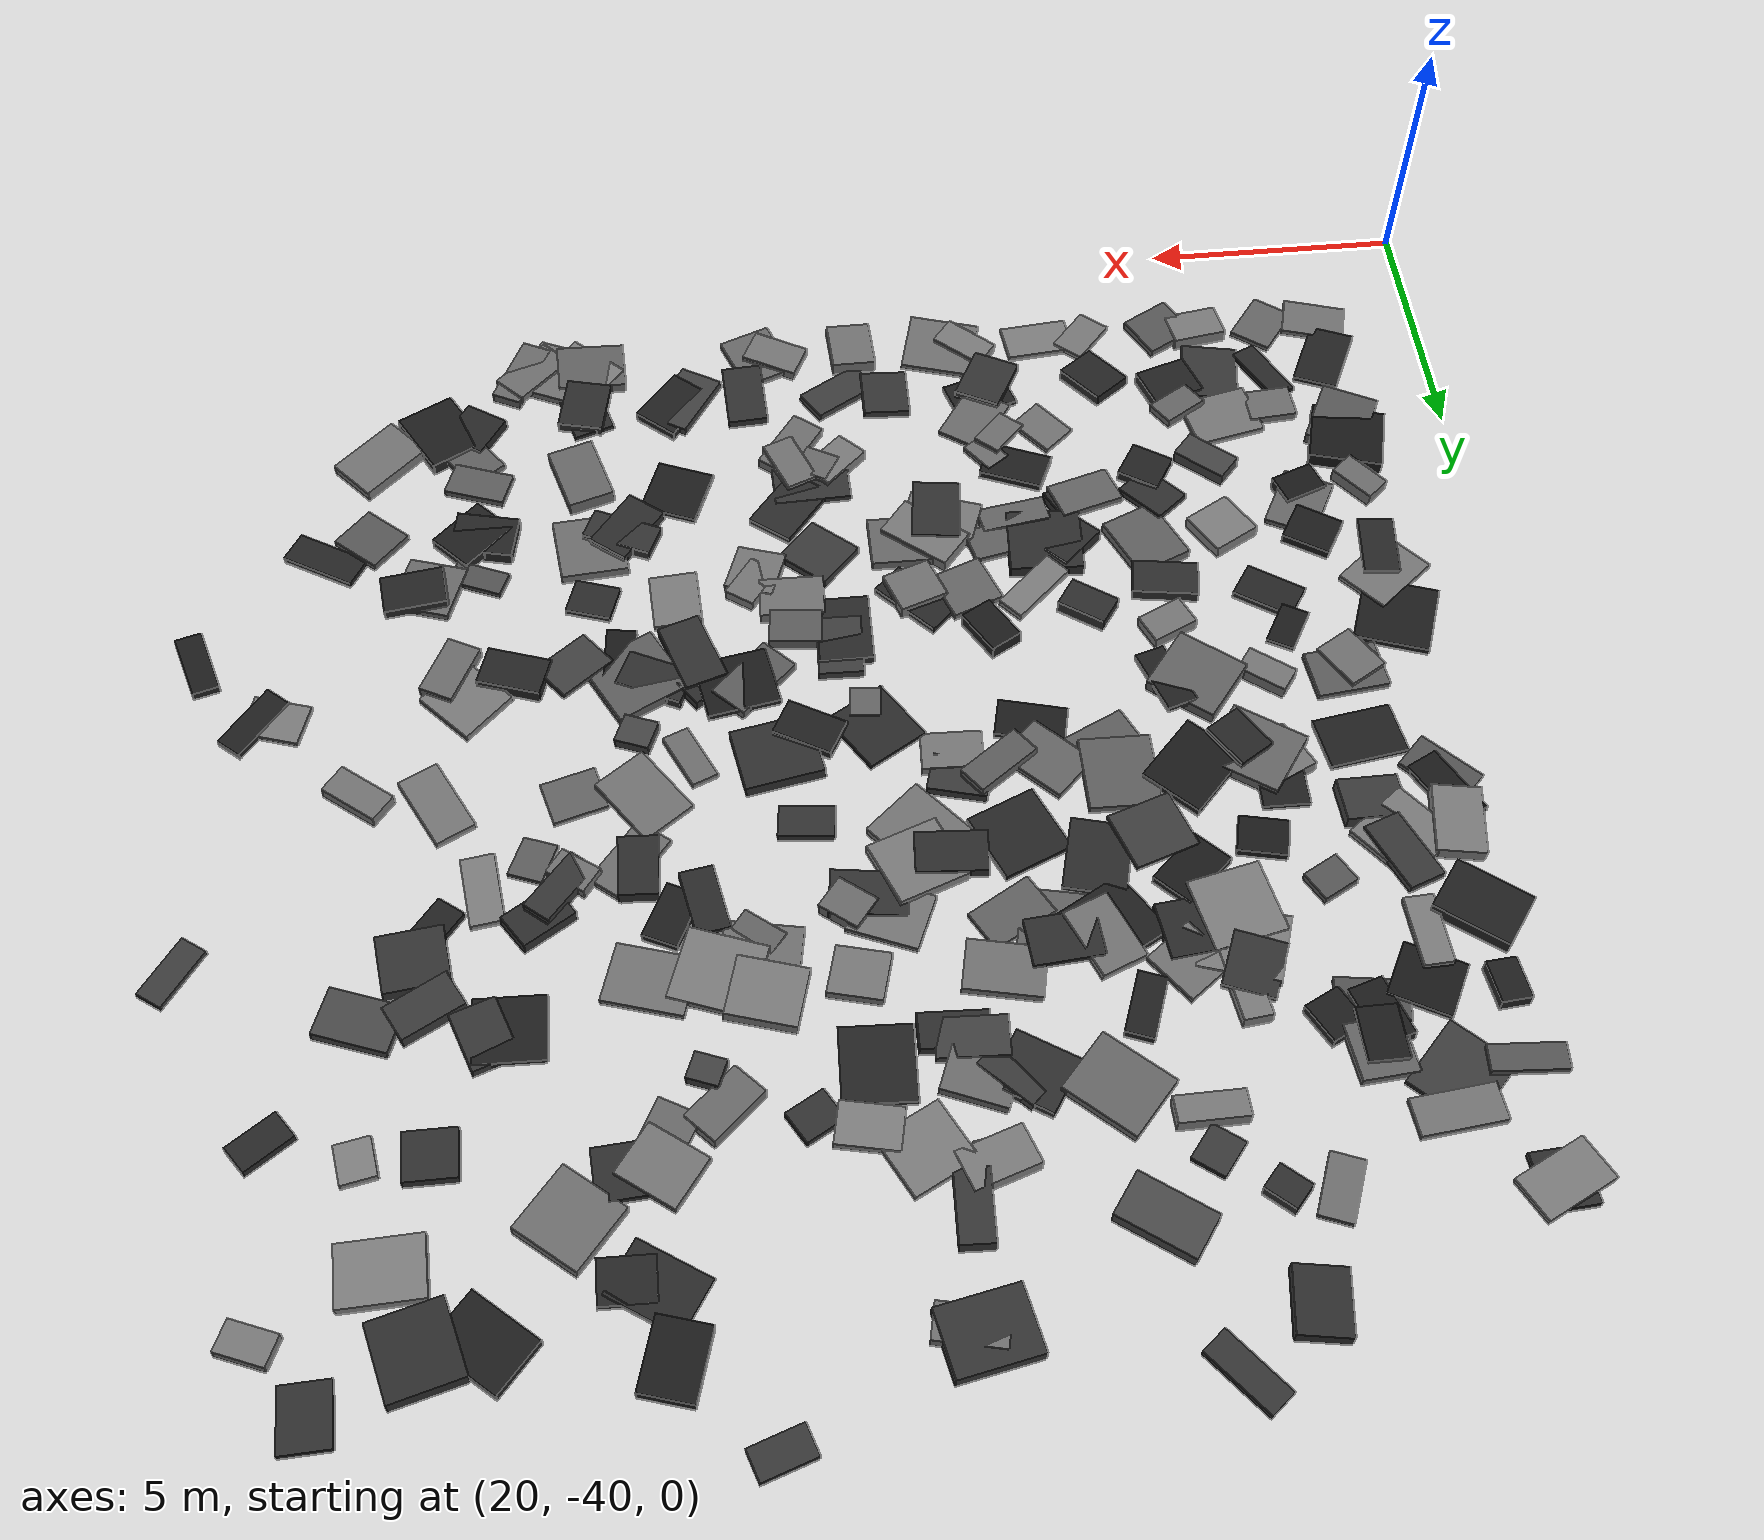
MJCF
<mujoco model="random_box_terrain">
    <compiler angle="degree" coordinate="local"/>
    <option timestep="0.01" gravity="0 0 -9.81" integrator="RK4"/>

    <worldbody>
    <body name="offset" pos="30 -30 0">
        <body name="terrain" pos="-8.0 -8.0 -0.1">
    <geom type="box" pos="0.0 0.0 0" size="0.417076661083997 0.6227710700655538 0.0651339855924607" euler="-2.064706443589345 -2.0807179985188196 75.35516787513157" rgba="0.4514152171694229 0.4514152171694229 0.4514152171694229 1"/>
<geom type="box" pos="0.0 1.0423145010082755 0" size="0.7310566865907171 0.4395334084925293 0.05994544506472791" euler="0.44068824363716796 2.4945157357201797 64.70940673724475" rgba="0.13233689642314755 0.13233689642314755 0.13233689642314755 1"/>
<geom type="box" pos="0.0 2.770731957955796 0" size="0.5620538903232275 0.7073575085101718 0.12981024928070697" euler="0.0014483142114718461 -1.214967717267734 153.68155304203864" rgba="0.34781760541305473 0.34781760541305473 0.34781760541305473 1"/>
<geom type="box" pos="0.0 3.240848087497372 0" size="0.7147996829931793 0.6941382401304935 0.14726687585038872" euler="2.192989509236389 -1.46335265289265 345.25744967768605" rgba="0.10223355325332335 0.10223355325332335 0.10223355325332335 1"/>
<geom type="box" pos="0.0 4.362121991804202 0.05044530447561758" size="0.45759801757686197 0.27162930427497856 0.14929103967424143" euler="-2.6261539329223043 -1.6937593573119503 130.75658653973562" rgba="0.43282076880994524 0.43282076880994524 0.43282076880994524 1"/>
<geom type="box" pos="0.0 6.066030764440578 0.10048904117251513" size="0.3402854523532605 0.6408174844852325 0.06106880962216909" euler="0.04498702478063876 1.1377657490864195 173.68363116960253" rgba="0.15166219022861235 0.15166219022861235 0.15166219022861235 1"/>
<geom type="box" pos="0.0 6.655135776014124 0.03194927244291473" size="0.528256294133354 0.7109635125649194 0.06309134108273251" euler="0.9322601012341374 0.7529143975286061 129.5215659672628" rgba="0.47079221774192004 0.47079221774192004 0.47079221774192004 1"/>
<geom type="box" pos="0.0 7.671262958099271 0" size="0.7080701405682928 0.7047990408367846 0.07759255002110241" euler="-1.308538246694314 2.198259818707278 159.67388368065434" rgba="0.1120973907959403 0.1120973907959403 0.1120973907959403 1"/>
<geom type="box" pos="0.0 11.20718090522312 0" size="0.3971130117470762 0.6530604679328992 0.05907151031891605" euler="-0.4030798548862524 -2.539463450475238 45.19096503403996" rgba="0.3384600010751079 0.3384600010751079 0.3384600010751079 1"/>
<geom type="box" pos="0.0 11.626445877786354 0.04585201510234593" size="0.7187981706498539 0.31833585843418516 0.07892243015657856" euler="0.6610515807179302 1.6341852077734282 296.5271679666282" rgba="0.10038387848127686 0.10038387848127686 0.10038387848127686 1"/>
<geom type="box" pos="0.0 12.377943847087337 0.12031193742956632" size="0.4485760270480471 0.685443282381075 0.13509704491895314" euler="-0.6856034903699344 -1.5873470919151371 351.0450747874064" rgba="0.4926103634608655 0.4926103634608655 0.4926103634608655 1"/>
<geom type="box" pos="0.0 14.120702190980964 0.1717525791644384" size="0.7305824061411731 0.569601139962564 0.13793154247739325" euler="2.178971481798415 -2.6030791304639083 322.9556877103257" rgba="0.12817861662777627 0.12817861662777627 0.12817861662777627 1"/>
<geom type="box" pos="0.0 17.104200565484756 0.26549782964248275" size="0.6597376581297126 0.2545279408813899 0.06514055049965828" euler="2.541887588911136 2.847734112734571 355.10289796216085" rgba="0.33599418957805394 0.33599418957805394 0.33599418957805394 1"/>
<geom type="box" pos="0.0 15.720164585709338 0.31894736582565936" size="0.400099552275453 0.2804904459640672 0.1265156630217813" euler="1.6986827441463905 -2.1635553349304555 96.4653061697635" rgba="0.12385891670677225 0.12385891670677225 0.12385891670677225 1"/>
<geom type="box" pos="0.0 19.31795820729961 0.381329213398535" size="0.4269000206157742 0.7060674151515058 0.06509492339675002" euler="-0.21606741813450192 1.4906352244441639 115.95909497584894" rgba="0.4879975880737527 0.4879975880737527 0.4879975880737527 1"/>
<geom type="box" pos="0.0 19.28718674385567 0.3112114840499406" size="0.5089276123632962 0.4530065019714603 0.0679059643458044" euler="-1.1658035766930406 -2.7214271210358425 274.93917687580785" rgba="0.18356147557222857 0.18356147557222857 0.18356147557222857 1"/>
<geom type="box" pos="1.082447424488493 0.0 0" size="0.5568197434821609 0.42022790982344105 0.062210290298896034" euler="0.2060727627447254 0.08874816557922394 233.01673955739196" rgba="0.40213394712759787 0.40213394712759787 0.40213394712759787 1"/>
<geom type="box" pos="1.3006005218387333 1.3198413073329405 0" size="0.6912268432023174 0.2567153342111516 0.05608444424453773" euler="0.7867844953815095 -0.4999841983655733 116.26609673046386" rgba="0.1615745595441876 0.1615745595441876 0.1615745595441876 1"/>
<geom type="box" pos="1.3497962070091947 2.2181141504983968 0" size="0.46366225495940794 0.3699918913058163 0.08699131963935601" euler="1.648332459251991 2.7079976944423203 182.52583645656605" rgba="0.42531712636559393 0.42531712636559393 0.42531712636559393 1"/>
<geom type="box" pos="1.2010565376729059 4.368213436785947 0" size="0.3017998121744597 0.42547207441667406 0.14647590565093174" euler="-2.8245284642282176 0.545450324255305 289.9725882633808" rgba="0.10041106313951326 0.10041106313951326 0.10041106313951326 1"/>
<geom type="box" pos="1.2711148176684746 4.805178270045847 0" size="0.4927666617980443 0.6580163506251767 0.06954021684348255" euler="-0.45942718416383954 2.0372442328519575 331.69485807492674" rgba="0.40373018373291725 0.40373018373291725 0.40373018373291725 1"/>
<geom type="box" pos="1.1924604013706483 5.592080729166449 0.0977212009642009" size="0.4097573126206789 0.4715485419356627 0.11109742305489986" euler="-2.850349430609251 -0.46388823074835983 59.08016966289597" rgba="0.10822608782002635 0.10822608782002635 0.10822608782002635 1"/>
<geom type="box" pos="1.2159671501433253 8.852195576394962 0" size="0.6907561496656047 0.47557886053595455 0.07423232428659299" euler="-2.3971842826332543 -0.8238983483206557 7.058829618622355" rgba="0.36479334411835873 0.36479334411835873 0.36479334411835873 1"/>
<geom type="box" pos="1.3011826039201946 10.378690023662937 0.05772740989820269" size="0.5124898864757529 0.7409665594328887 0.05509007217560905" euler="-0.4330614887412718 1.1436824443675055 98.48100633867863" rgba="0.12579376846701235 0.12579376846701235 0.12579376846701235 1"/>
<geom type="box" pos="1.0917666191901516 8.626268467265815 0" size="0.4012712660322762 0.49647311128287225 0.14131481217858866" euler="0.1394029205780436 1.2579785472088103 30.307112898945977" rgba="0.4390696150743101 0.4390696150743101 0.4390696150743101 1"/>
<geom type="box" pos="1.4019834385928074 11.749075515673322 0.04248129452104989" size="0.4340182324731727 0.5646805791279709 0.13931619864037198" euler="2.413357287338428 -2.1400942453981044 92.16219406608573" rgba="0.2345325953021741 0.2345325953021741 0.2345325953021741 1"/>
<geom type="box" pos="1.0029168053883024 12.538517040831085 0.1136090700944548" size="0.6721343188227764 0.6793149918753691 0.07319239929736951" euler="0.16821176132342464 0.03412904533898242 307.53555308440804" rgba="0.4836825637347706 0.4836825637347706 0.4836825637347706 1"/>
<geom type="box" pos="1.1039269023221598 12.929537847878143 0.16492642343756808" size="0.363933916917664 0.7176954818078389 0.0822436990746701" euler="2.4118481707332933 -1.4953899273144355 21.6247019018706" rgba="0.2243711068763169 0.2243711068763169 0.2243711068763169 1"/>
<geom type="box" pos="1.3254772012917906 17.85650375660137 0.11085390877836829" size="0.347337837317268 0.7499317351389125 0.0720930664770709" euler="-0.24377744684260083 2.9761868706249093 95.15474500032339" rgba="0.45562424197664264 0.45562424197664264 0.45562424197664264 1"/>
<geom type="box" pos="1.2475851940536735 15.413189843635315 0.0629376149303554" size="0.5559908972324248 0.5780024892043747 0.05664813438839087" euler="1.968733982790524 -1.492641256688988 241.69390054522304" rgba="0.10236608875137572 0.10236608875137572 0.10236608875137572 1"/>
<geom type="box" pos="1.039384076415216 14.513780053256365 0.13089766958824078" size="0.6764613795561717 0.2711513492299715 0.07768209609605442" euler="0.6546060965753489 1.7149184389052259 92.52476614624915" rgba="0.48765660102794617 0.48765660102794617 0.48765660102794617 1"/>
<geom type="box" pos="1.0902747923541434 17.17509542395864 0.035157977768194335" size="0.6509314548604532 0.729460234065705 0.056206650528491664" euler="-0.7941420177229568 -1.4153274899470387 316.24415905465776" rgba="0.24321070795241015 0.24321070795241015 0.24321070795241015 1"/>
<geom type="box" pos="2.4924830334135066 0.0 0.042805795546767736" size="0.5383727188773557 0.3539074206400143 0.13445252382314715" euler="0.3635503586130162 -0.5073119607229 189.75890888643877" rgba="0.483860884801408 0.483860884801408 0.483860884801408 1"/>
<geom type="box" pos="2.394967850130382 1.2461674939880811 0" size="0.6644383330258128 0.5522426607096843 0.06788218523414005" euler="-0.9547482718555016 -2.926386520571131 81.77365034899488" rgba="0.21836885005881057 0.21836885005881057 0.21836885005881057 1"/>
<geom type="box" pos="2.3776800317775804 2.435062910662701 0" size="0.6975025980619405 0.5546526846093112 0.06211536987368069" euler="-0.9880947056001346 -0.49534656483312567 12.705779865350117" rgba="0.47305853272900966 0.47305853272900966 0.47305853272900966 1"/>
<geom type="box" pos="2.8943956960231088 3.546924913172756 0.04605285446711388" size="0.5484699538720841 0.29249273994870817 0.1406699016285174" euler="-0.44935326356780525 2.280182364567839 137.94018782013345" rgba="0.27142206908810396 0.27142206908810396 0.27142206908810396 1"/>
<geom type="box" pos="2.9118206071884445 5.295857164230253 0.07798121657109643" size="0.47852804129133214 0.48297822635582116 0.1296041750069171" euler="1.5083175440245506 2.042045162460771 118.8054921247891" rgba="0.4922113116244452 0.4922113116244452 0.4922113116244452 1"/>
<geom type="box" pos="2.2926444171354463 6.9304458571720415 0.025042940169248448" size="0.5863056807579865 0.3869148660852408 0.07371584118266303" euler="2.8751521004051135 -2.232532522095677 146.6547505604044" rgba="0.14698646013456484 0.14698646013456484 0.14698646013456484 1"/>
<geom type="box" pos="2.712318327607656 8.79361846977695 0.04729627482677283" size="0.47957497695681023 0.25810991033214187 0.14512472110189062" euler="-1.944838985318493 0.28867587616624135 323.5993212405711" rgba="0.4630942178562423 0.4630942178562423 0.4630942178562423 1"/>
<geom type="box" pos="2.1282381186808936 7.843538657614528 0.11222521171396917" size="0.26551458840118364 0.4631470118734512 0.050315780251087364" euler="1.6846065860918396 0.40316860904594964 330.21721135684055" rgba="0.1060145585059658 0.1060145585059658 0.1060145585059658 1"/>
<geom type="box" pos="2.949344059696669 10.699651287496202 0" size="0.504489592477864 0.5618789783189184 0.13258037023378674" euler="-0.48462292171557086 2.1525927221232655 295.2036336079021" rgba="0.4668789659835152 0.4668789659835152 0.4668789659835152 1"/>
<geom type="box" pos="2.9173281281927905 11.020227151381567 0.06490747636318382" size="0.7426403684309055 0.4288277746860365 0.050102432064855096" euler="2.6268880884567016 1.166873699669802 268.6990188131561" rgba="0.12509425452346906 0.12509425452346906 0.12509425452346906 1"/>
<geom type="box" pos="2.4584958165364745 13.268117733998935 0.023028829454557337" size="0.36244423326665987 0.3054951681746396 0.09024976469730162" euler="-0.056695435890333545 2.2392403173378446 27.80719814584133" rgba="0.33638845125752215 0.33638845125752215 0.33638845125752215 1"/>
<geom type="box" pos="2.9413180282468634 15.915945875535904 0" size="0.39718686345864523 0.3616441261976391 0.10994882298035305" euler="0.8910022208813801 -2.0340586830500924 117.52805730449532" rgba="0.11818168387887185 0.11818168387887185 0.11818168387887185 1"/>
<geom type="box" pos="2.254679285405109 15.664423486160716 0" size="0.6428033942086084 0.3880140423101759 0.07276267266328293" euler="2.679518602467434 2.1189491055715557 170.29339742985147" rgba="0.3277435660431304 0.3277435660431304 0.3277435660431304 1"/>
<geom type="box" pos="2.261244522506139 16.37216439077837 0.07849187376202599" size="0.361219613762276 0.5100217053700953 0.11831387927418982" euler="-0.11632364301179443 0.2879050309094344 0.7118923591525128" rgba="0.1103079637240728 0.1103079637240728 0.1103079637240728 1"/>
<geom type="box" pos="2.3218427785709403 16.61582626662638 0.036171319759196296" size="0.5371642298049781 0.5086495957568967 0.08914491322687855" euler="1.3489779628457566 -1.3869710803645487 95.59752337840631" rgba="0.4015162845655248 0.4015162845655248 0.4015162845655248 1"/>
<geom type="box" pos="2.16265277243818 15.942051185899162 0" size="0.3324274970828504 0.5800522243101278 0.12794926789312147" euler="1.1052517386679046 1.2053064830993403 17.087306292160026" rgba="0.1053979344981578 0.1053979344981578 0.1053979344981578 1"/>
<geom type="box" pos="3.2500483649007528 0.0 0.08480181568293493" size="0.4653216963287955 0.5190300198545825 0.08875873748605667" euler="-2.2935139697339135 -0.577996526806289 118.79520703816983" rgba="0.34796165225844816 0.34796165225844816 0.34796165225844816 1"/>
<geom type="box" pos="3.2681852610925053 1.4802773826018776 0" size="0.4369913376682958 0.5309084685297877 0.13360721328682043" euler="-0.6184437653596184 -2.1569164201728075 109.15275380929764" rgba="0.14110146523817255 0.14110146523817255 0.14110146523817255 1"/>
<geom type="box" pos="3.2246218486201044 2.1239532521573077 0.08154619040329045" size="0.4570398440197517 0.2861369304492373 0.09753469411013588" euler="2.421873516661509 2.94110909314106 30.82348535894692" rgba="0.39342781894242995 0.39342781894242995 0.39342781894242995 1"/>
<geom type="box" pos="4.1422889527627005 3.7157756117299416 0.08890396647340454" size="0.415886546215263 0.4116942572927613 0.10861912467356304" euler="0.8553493993404793 -2.163232317341209 328.6401726249596" rgba="0.14093353786535637 0.14093353786535637 0.14093353786535637 1"/>
<geom type="box" pos="4.416188675359459 5.458737719380879 0.02141565728475199" size="0.5632265396032221 0.6718301540418932 0.10905852985880107" euler="0.05838618934930295 -1.0599693236781738 203.8390196512372" rgba="0.37836646369526095 0.37836646369526095 0.37836646369526095 1"/>
<geom type="box" pos="4.22183787760805 6.492451356634304 0.0645516051612991" size="0.6247051621628071 0.37501388547822073 0.12195856663554056" euler="1.0841733926498538 1.0907131412783446 170.6465970276127" rgba="0.1750082577523293 0.1750082577523293 0.1750082577523293 1"/>
<geom type="box" pos="4.040386067806793 8.820687413640666 0.11795594009895767" size="0.6492205971919442 0.6922781430752137 0.14565305620886598" euler="-2.2571344131428073 2.1823839747143845 231.36426337464945" rgba="0.3847799138453356 0.3847799138453356 0.3847799138453356 1"/>
<geom type="box" pos="3.5484268116367557 10.337379596996804 0.2056002382996714" size="0.37185494981584655 0.4719525036980523 0.14422027029089507" euler="-1.469400847191092 -1.5844542893676894 212.50580870428777" rgba="0.15402133095629741 0.15402133095629741 0.15402133095629741 1"/>
<geom type="box" pos="3.2700353627001473 10.51841167190518 0.08725462072486867" size="0.6831218225115692 0.7317961388457516 0.11280772675800473" euler="1.5909826005915164 0.36913983179499565 54.60232942852537" rgba="0.40297241516551685 0.40297241516551685 0.40297241516551685 1"/>
<geom type="box" pos="4.455091372868951 10.793197353361965 0.1158759791252985" size="0.7370667036156973 0.6101209448223063 0.09865090968008076" euler="-2.104115446101255 -0.735904684657334 46.73609940756952" rgba="0.10289638466423608 0.10289638466423608 0.10289638466423608 1"/>
<geom type="box" pos="4.11569959929678 14.972692309827117 0" size="0.3059929675511405 0.42722882443996024 0.0590758347460182" euler="1.4143668259417455 2.031312912405789 247.1572310139974" rgba="0.30507979833767673 0.30507979833767673 0.30507979833767673 1"/>
<geom type="box" pos="3.463345547611792 12.304642723582912 0" size="0.452895972487537 0.3529387710955445 0.09712461174280802" euler="-2.2098877991752586 1.3994961216186006 347.1477523397636" rgba="0.10265404206499062 0.10265404206499062 0.10265404206499062 1"/>
<geom type="box" pos="4.20861144858045 14.390947601053206 0" size="0.6544656583558763 0.7401166150714928 0.1085760805770769" euler="1.672824552536344 2.7970086778803847 71.12606632220387" rgba="0.4866474466438063 0.4866474466438063 0.4866474466438063 1"/>
<geom type="box" pos="4.353879628439326 18.90142257505701 0" size="0.26253665303113677 0.31783747835777687 0.13836193517310255" euler="-0.7639665580884003 1.3080561984967343 228.0639256192834" rgba="0.17967002802793375 0.17967002802793375 0.17967002802793375 1"/>
<geom type="box" pos="3.5050389560237596 18.996855075735706 0.05408160364198494" size="0.576255387827258 0.30293616447700544 0.05872880996225698" euler="-0.26231979404476746 0.9514458575664326 68.20570519577532" rgba="0.43358759647687684 0.43358759647687684 0.43358759647687684 1"/>
<geom type="box" pos="4.209329255609524 20.837907369009216 0" size="0.46456332594451155 0.5944729099679276 0.12310832578023624" euler="1.9203270187574324 -2.6360517821826526 171.72230956561808" rgba="0.18787014559305334 0.18787014559305334 0.18787014559305334 1"/>
<geom type="box" pos="4.853106334978193 0.0 0.0034859168788690664" size="0.32166934682419973 0.5388926585986963 0.06288390430176682" euler="1.8459830599312124 -2.32973267722436 140.13381766374425" rgba="0.48211704832428914 0.48211704832428914 0.48211704832428914 1"/>
<geom type="box" pos="4.765519374532638 1.17430189608895 0.041132097286068134" size="0.4249286731012197 0.5233882268360652 0.11796882508796579" euler="2.668238469443267 0.039805430425494226 37.3624974359974" rgba="0.14014431993273938 0.14014431993273938 0.14014431993273938 1"/>
<geom type="box" pos="5.9941849498106095 2.3934920087073066 0" size="0.46667956318032955 0.37073582256000126 0.058932839275341875" euler="-2.844712282380426 -1.916640126873277 310.7264753741245" rgba="0.45543582989739606 0.45543582989739606 0.45543582989739606 1"/>
<geom type="box" pos="4.102196859165359 4.360193841866973 0.07078915571720476" size="0.4018039568831147 0.5136593535794217 0.07786361661958" euler="2.9546902271495696 -0.7643367523086968 40.51377659334825" rgba="0.18679536006618488 0.18679536006618488 0.18679536006618488 1"/>
<geom type="box" pos="5.4200261142309785 4.247323354438685 0.08819038812489657" size="0.4035604614160354 0.6268803034277275 0.0718198956822555" euler="2.796264243901015 0.588102725226876 286.4398120618386" rgba="0.3958317845612266 0.3958317845612266 0.3958317845612266 1"/>
<geom type="box" pos="5.7759964029809865 6.965172220093829 0.11182197180721332" size="0.32173651615287396 0.48058939600067674 0.13713549231096497" euler="1.3371958303787768 -0.8692762314923295 235.26270318166337" rgba="0.18117610761148828 0.18117610761148828 0.18117610761148828 1"/>
<geom type="box" pos="4.351106319651726 7.495278143991346 0.06820742915543257" size="0.454877899433152 0.3028218390123062 0.1330139097349548" euler="-1.225433960582695 2.3658286743484824 203.61851917871115" rgba="0.4601778593807718 0.4601778593807718 0.4601778593807718 1"/>
<geom type="box" pos="4.6174948462510885 8.837285126027918 0.16690692308494445" size="0.6751502068585787 0.2963452162513952 0.058215479782577975" euler="2.682604579568922 0.08036006759531222 107.500363108402" rgba="0.12827207728469603 0.12827207728469603 0.12827207728469603 1"/>
<geom type="box" pos="5.987804875841033 9.963419622276204 0" size="0.3399600164094716 0.6322095081939629 0.06013466147440144" euler="-0.6571170412161571 2.0168205417211995 114.67243146851604" rgba="0.3641148677000543 0.3641148677000543 0.3641148677000543 1"/>
<geom type="box" pos="4.829189292729353 12.84718322750661 0" size="0.6109036660146563 0.40684968540702027 0.09074433029491642" euler="1.8360473530860109 -0.3348493135342814 223.7911245979238" rgba="0.10379478824118507 0.10379478824118507 0.10379478824118507 1"/>
<geom type="box" pos="4.205883567732904 13.711612298418842 0.07516929896880828" size="0.695128812641586 0.6717911510347794 0.09105386069618471" euler="-2.48835855447778 2.086839274975109 101.80895929514497" rgba="0.49280846034049175 0.49280846034049175 0.49280846034049175 1"/>
<geom type="box" pos="5.396326990221467 12.04389452549867 0.09262927945182875" size="0.5666326133626494 0.6222125486826791 0.050927185767984544" euler="-2.507032388908974 -2.155757754466311 289.46825887733075" rgba="0.24801051146585704 0.24801051146585704 0.24801051146585704 1"/>
<geom type="box" pos="4.333365382572651 15.173672650304276 0" size="0.26592529463628883 0.7214346976468071 0.1296702825550514" euler="2.551779990764693 0.3983150339635708 6.883802652302511" rgba="0.48810755645890247 0.48810755645890247 0.48810755645890247 1"/>
<geom type="box" pos="4.118555925087934 14.8721509922442 0.09522955498270524" size="0.5508592641932665 0.47630977702247723 0.06378593308336496" euler="-1.398027409619171 -0.4809398150084725 247.90528495746605" rgba="0.2036185836670623 0.2036185836670623 0.2036185836670623 1"/>
<geom type="box" pos="5.186212754611799 14.654165516383202 0.008274945299228814" size="0.5374918917005937 0.5123862715246518 0.06755996694896643" euler="-2.850516676765162 1.0059737829869562 126.81128765954398" rgba="0.44860181185526704 0.44860181185526704 0.44860181185526704 1"/>
<geom type="box" pos="5.568666553254321 21.82846512789554 0" size="0.2708182870724112 0.7052755175406185 0.07059434481129055" euler="-0.600829933537709 -1.1131942995074167 219.1034718033001" rgba="0.2117082200371518 0.2117082200371518 0.2117082200371518 1"/>
<geom type="box" pos="5.761244813904711 0.0 0" size="0.4197011667136451 0.6719696845651424 0.05454008842917059" euler="2.596990978440303 0.4626917710598337 275.2263130206634" rgba="0.4975054622815107 0.4975054622815107 0.4975054622815107 1"/>
<geom type="box" pos="7.122336315481089 1.412430836944315 0" size="0.46226397390269536 0.6099351221690978 0.05614780587561405" euler="0.9124259770102734 2.4675682312203193 285.5405913667307" rgba="0.12240598614678269 0.12240598614678269 0.12240598614678269 1"/>
<geom type="box" pos="6.883886750527303 2.5260611491718863 0.09363418582366656" size="0.2768930817301952 0.43129321478243493 0.056778213263672765" euler="1.1625377832784363 0.745708251783924 317.4928550308561" rgba="0.4339952045239561 0.4339952045239561 0.4339952045239561 1"/>
<geom type="box" pos="5.771413172233617 4.258059479493746 0" size="0.2596660313570239 0.3900729013687968 0.10610076258901188" euler="2.7188150044461743 -1.9151469595642268 114.28099647267645" rgba="0.1505315063579301 0.1505315063579301 0.1505315063579301 1"/>
<geom type="box" pos="7.114254859219653 5.175723460494344 0.04708361076096404" size="0.7156102160487154 0.3587109010338853 0.06380852299374104" euler="-1.4466747849825958 -1.7064341857648975 193.13700409294515" rgba="0.3861503712524764 0.3861503712524764 0.3861503712524764 1"/>
<geom type="box" pos="5.869252378451844 5.3615075164873645 0" size="0.5281254283367627 0.32721917930938393 0.13461289212537722" euler="2.195822615428354 1.32937657716999 43.23453029357667" rgba="0.16831030463723745 0.16831030463723745 0.16831030463723745 1"/>
<geom type="box" pos="6.722730274704986 6.439345136357083 0.07557131098272882" size="0.2629303773694338 0.7131026665609907 0.08203931895647304" euler="-2.9469613278785385 -0.5899515586504327 312.59426229377834" rgba="0.49670332045137966 0.49670332045137966 0.49670332045137966 1"/>
<geom type="box" pos="7.2052046558437475 9.476876504587057 0.010357828942866562" size="0.38091377586898234 0.6465564450350545 0.06532777498585379" euler="0.0027519464661081017 -1.4278977109492796 76.75313726536378" rgba="0.11136471472128587 0.11136471472128587 0.11136471472128587 1"/>
<geom type="box" pos="5.783625236200688 10.769063233754968 0.07519157596093351" size="0.7417474518415847 0.6591973118103316 0.08123328771292475" euler="0.050958396846295884 -1.1571810649231553 90.0323480247418" rgba="0.3743087670340427 0.3743087670340427 0.3743087670340427 1"/>
<geom type="box" pos="6.428289358865362 12.447540842314137 0" size="0.7104083621583864 0.5662258612389575 0.06377379242164474" euler="-1.96922042224914 0.9888538250482624 75.32232642997222" rgba="0.16674980539123388 0.16674980539123388 0.16674980539123388 1"/>
<geom type="box" pos="7.3056780424582275 13.702513749715123 0" size="0.624085527929858 0.6948212044410054 0.052910318784945856" euler="0.12015941052934087 0.4957205168747354 77.61193553936839" rgba="0.39025816265256874 0.39025816265256874 0.39025816265256874 1"/>
<geom type="box" pos="7.27380494839376 14.051157050566687 0.0999504875026482" size="0.6376440503933773 0.4607933143316678 0.06244987868222554" euler="0.07822307962338026 1.949774737914895 183.9779879641397" rgba="0.17343630255154718 0.17343630255154718 0.17343630255154718 1"/>
<geom type="box" pos="5.341483598771637 17.440423205777638 0.07779243251048622" size="0.250199377718241 0.6211197529960715 0.14405809886175402" euler="1.0924261112146318 -0.8639600716298066 91.52439943416002" rgba="0.4823402425212052 0.4823402425212052 0.4823402425212052 1"/>
<geom type="box" pos="5.079005555084044 14.015825610906955 0" size="0.5467514325370068 0.4971652030663521 0.10442920146434737" euler="0.40163032056320347 -0.8915397895389154 96.82759675776936" rgba="0.1661909659926994 0.1661909659926994 0.1661909659926994 1"/>
<geom type="box" pos="6.575259614678981 14.055796649667469 0.07549898107945807" size="0.6729163560796525 0.45002285040825646 0.0901494356371895" euler="-2.2719648952795595 -2.965125822062168 113.12457455150431" rgba="0.4602104776095678 0.4602104776095678 0.4602104776095678 1"/>
<geom type="box" pos="5.340550029412762 18.149228705711057 0" size="0.3229454836805363 0.36964600255082736 0.05741022267698287" euler="1.9265656407964329 2.699690009493768 141.2780560372059" rgba="0.22735521734281194 0.22735521734281194 0.22735521734281194 1"/>
<geom type="box" pos="7.763962441994261 0.0 0" size="0.6538248491763147 0.6985472453069934 0.0633760530140729" euler="-2.936739976547398 -1.1226132656625747 74.90428858809449" rgba="0.4507628886379411 0.4507628886379411 0.4507628886379411 1"/>
<geom type="box" pos="6.942588518227509 1.0980483800600205 0.06656729458382854" size="0.5918285747641854 0.46111627747694467 0.10871847308802937" euler="1.3320263354596094 -0.1877412192996495 62.2836194035592" rgba="0.20059585445495257 0.20059585445495257 0.20059585445495257 1"/>
<geom type="box" pos="7.308141805544499 2.052536335929141 0.017062746501750728" size="0.4643984990345897 0.6403995572734548 0.05361473333020059" euler="-2.1252692863544187 1.5479657479136257 325.0650826732393" rgba="0.42188448118694577 0.42188448118694577 0.42188448118694577 1"/>
<geom type="box" pos="6.658160249051255 3.3508072914308613 0" size="0.6223671225824933 0.39778901259114685 0.08261516641054695" euler="1.769224955924268 1.4567814899639329 335.8731591401777" rgba="0.12152184375276974 0.12152184375276974 0.12152184375276974 1"/>
<geom type="box" pos="6.875845831737626 4.656647279821637 0" size="0.6595590482006792 0.27687050368813826 0.14938673167308011" euler="2.2329403488785813 2.8996932768975405 7.3075791081017405" rgba="0.3884293156744689 0.3884293156744689 0.3884293156744689 1"/>
<geom type="box" pos="6.361023294570558 5.317710847708317 0" size="0.677101108755668 0.7062119086770922 0.1377843916610102" euler="-1.9309761818603992 0.6509166712552901 86.80813665446186" rgba="0.17693466935454494 0.17693466935454494 0.17693466935454494 1"/>
<geom type="box" pos="7.997185435006999 6.328306008884081 0.05598799712679725" size="0.510049185930638 0.5020882517956238 0.08042746421711307" euler="-1.8636180086891019 0.21987725339146635 200.6777686945148" rgba="0.40144967191887737 0.40144967191887737 0.40144967191887737 1"/>
<geom type="box" pos="7.655624610122883 7.311167046767999 0.054249658430337536" size="0.32379780928812213 0.48768298750616845 0.1486326519937481" euler="0.547709831029521 1.6257871992542947 29.46758393620259" rgba="0.1059453012913127 0.1059453012913127 0.1059453012913127 1"/>
<geom type="box" pos="7.930604829374921 10.395925400100284 0.15395798060879218" size="0.29232556759513206 0.6700004944031169 0.1251043251173184" euler="0.9141132875646978 0.5442428880431374 126.35080856839717" rgba="0.3632663301397727 0.3632663301397727 0.3632663301397727 1"/>
<geom type="box" pos="7.738590288893672 11.831897596631396 0" size="0.6845565452175739 0.6751679216432886 0.05852063205025631" euler="-0.1780003013610405 -0.36930803357748676 113.33779858069917" rgba="0.1524712967828247 0.1524712967828247 0.1524712967828247 1"/>
<geom type="box" pos="8.088156793092553 13.427389700550489 0" size="0.6418116066105437 0.41731872000444203 0.05332813530971811" euler="-1.9257152955990657 2.96993348572647 209.0236386070019" rgba="0.37503107097931465 0.37503107097931465 0.37503107097931465 1"/>
<geom type="box" pos="6.07591151500292 15.429040173933801 0" size="0.2666459481424877 0.6172166699318109 0.08982625805169892" euler="2.2326125362041633 -1.9970781008978322 159.6810068567332" rgba="0.12816923872643288 0.12816923872643288 0.12816923872643288 1"/>
<geom type="box" pos="6.776019056101145 16.87899083051937 0.07069199149640402" size="0.7391518607939178 0.6388638784240557 0.09928151952282785" euler="-0.27861081438901625 -1.8708560227265303 138.53937831467758" rgba="0.4104872101630682 0.4104872101630682 0.4104872101630682 1"/>
<geom type="box" pos="6.3813672435376585 13.7947462020603 0" size="0.7051038980112833 0.6885247123069491 0.08554513562352445" euler="2.90098181488554 -1.1984666598846667 210.73427644060337" rgba="0.12183044234908157 0.12183044234908157 0.12183044234908157 1"/>
<geom type="box" pos="8.926960208224576 17.96760763729464 0" size="0.6206493757411178 0.3810627108918617 0.1346512353833746" euler="0.6813390439095519 -0.6508320828383622 199.14213250785238" rgba="0.4928860112001926 0.4928860112001926 0.4928860112001926 1"/>
<geom type="box" pos="6.384712245787339 19.199757517833408 0" size="0.4399678510422132 0.7494236054932293 0.14057840950359152" euler="-0.23976091331815041 -0.11212566070454333 54.17476510666282" rgba="0.2924087760962518 0.2924087760962518 0.2924087760962518 1"/>
<geom type="box" pos="7.269183965862813 0.0 0" size="0.30443642081888406 0.5495211226456718 0.12226642211585918" euler="-2.780344990787592 -1.799264744712549 50.423766718308954" rgba="0.4954726927295704 0.4954726927295704 0.4954726927295704 1"/>
<geom type="box" pos="9.034071178019982 1.2538609474322904 0.05959825644099351" size="0.5129891157891839 0.45635635409591424 0.08738478257272804" euler="-2.02149945656019 -2.0258942117499323 269.1960037850874" rgba="0.21044431380320594 0.21044431380320594 0.21044431380320594 1"/>
<geom type="box" pos="7.191278093158832 2.95138805877332 0" size="0.2514251148644061 0.3750835087003528 0.065117899484695" euler="1.4551346790725095 2.9057979457196703 214.4987596636395" rgba="0.4322655628804305 0.4322655628804305 0.4322655628804305 1"/>
<geom type="box" pos="8.368830279126312 4.4421670027203515 0.06879814811933342" size="0.6817109757534334 0.4605437320613665 0.14536112253459385" euler="2.152933875692174 0.16575377032798766 82.22881874645036" rgba="0.19043053513222966 0.19043053513222966 0.19043053513222966 1"/>
<geom type="box" pos="8.640900700969548 4.977246507448098 0.06919525178927004" size="0.4291638606534381 0.73783035550276 0.1351802893296459" euler="-0.5850466647995463 1.3545693036720765 230.19412002637446" rgba="0.4762557122353266 0.4762557122353266 0.4762557122353266 1"/>
<geom type="box" pos="8.973098090684077 6.459127724806912 0" size="0.7215987939237329 0.35776156398421877 0.07486797017401287" euler="-0.10941571394411254 -1.4873400773655656 134.24561571620475" rgba="0.15637139545593426 0.15637139545593426 0.15637139545593426 1"/>
<geom type="box" pos="10.175638714290743 8.796933306501444 0" size="0.2962325364064255 0.28292929635917274 0.14366014340875388" euler="-2.2273199424561096 0.8473146006439944 265.0103669566824" rgba="0.39208611809336313 0.39208611809336313 0.39208611809336313 1"/>
<geom type="box" pos="10.034580520279771 9.337753169250531 0.04956953574065572" size="0.671259163463749 0.620144708478914 0.05014946329654757" euler="1.360791440232994 0.5542310189797663 301.5333946716251" rgba="0.16770878438297734 0.16770878438297734 0.16770878438297734 1"/>
<geom type="box" pos="8.725157929023121 9.987299312708151 0" size="0.38989017844630075 0.5611626091495068 0.10082337478643011" euler="2.1566952298247575 2.8712540195783802 266.6408280893039" rgba="0.46203470024978344 0.46203470024978344 0.46203470024978344 1"/>
<geom type="box" pos="8.999988575517854 12.186244173719908 0.0961706269788768" size="0.4026610528179478 0.6514671999446601 0.12186359017777706" euler="-2.083270471138361 0.7991721292741971 266.21921836354534" rgba="0.17329543947075315 0.17329543947075315 0.17329543947075315 1"/>
<geom type="box" pos="7.036303833640328 10.336381579225273 0.059495942113804955" size="0.5045196558630383 0.6715178515206881 0.0711018747839159" euler="-0.004220381810358997 1.0718585379743955 224.4311527375281" rgba="0.39841120067790403 0.39841120067790403 0.39841120067790403 1"/>
<geom type="box" pos="8.114467401838477 16.486030380237914 0" size="0.5579847036898559 0.6096736138535517 0.09805048027566819" euler="0.2473377119617517 0.9926485287068969 56.780352287585856" rgba="0.18029547133564222 0.18029547133564222 0.18029547133564222 1"/>
<geom type="box" pos="9.599819749116374 12.284132718109607 0.06399321977005193" size="0.6488707973291623 0.689685302152514 0.10235565274786863" euler="2.171532867160339 -2.3336220990238754 112.15525766905199" rgba="0.4945885810928624 0.4945885810928624 0.4945885810928624 1"/>
<geom type="box" pos="9.360442961844477 15.59908577485072 0" size="0.6193159861148109 0.33137908518168385 0.12413039211387558" euler="-2.8308877011573523 -1.6895566724979416 358.80170743934235" rgba="0.180164662806141 0.180164662806141 0.180164662806141 1"/>
<geom type="box" pos="10.064148912475172 17.707814907743657 0.07301517329420765" size="0.6325932982480154 0.6115191655102075 0.06401529861459365" euler="-1.2616684710111385 0.27408343440722227 27.46419512542932" rgba="0.493864597412098 0.493864597412098 0.493864597412098 1"/>
<geom type="box" pos="9.078265116245994 15.778240880288447 0.06633935175095203" size="0.37412453873925794 0.6296964583149189 0.08661875206483703" euler="-1.3434567418426058 2.812035836953065 86.52552934457923" rgba="0.2515912354893268 0.2515912354893268 0.2515912354893268 1"/>
<geom type="box" pos="11.160395707960964 0.0 0.06987345640356636" size="0.5596733999213537 0.36220807967204877 0.10572949283233748" euler="-1.1803025131882967 -2.766807900349195 333.6093368574483" rgba="0.4753506143789955 0.4753506143789955 0.4753506143789955 1"/>
<geom type="box" pos="9.966948595404201 1.072103567936805 0" size="0.337846648378355 0.6954072590461937 0.08363639221511578" euler="-0.0644656436119595 -1.4642262235703039 301.6410613328436" rgba="0.24338410714233874 0.24338410714233874 0.24338410714233874 1"/>
<geom type="box" pos="11.034661313529172 2.4359341746433367 0" size="0.6791341350390012 0.32687301079424325 0.11450819366356317" euler="-1.9218536172262317 -2.725463062608762 54.289465744047234" rgba="0.44439318434961805 0.44439318434961805 0.44439318434961805 1"/>
<geom type="box" pos="10.711317564555335 3.4288244889628414 0" size="0.44902271805486454 0.7425386163995997 0.06394103426740144" euler="2.370452064470933 1.3926436578033687 90.92687898086105" rgba="0.21111934877847072 0.21111934877847072 0.21111934877847072 1"/>
<geom type="box" pos="8.269605908928504 4.546388361120633 0" size="0.7090953962913287 0.43330094098088884 0.14278668541917147" euler="-0.9611435326382023 2.0246412153645847 159.8167984001138" rgba="0.4739119137354689 0.4739119137354689 0.4739119137354689 1"/>
<geom type="box" pos="10.521331532804963 7.436718832308943 0" size="0.6367576601709766 0.4231870271804965 0.09766404680342881" euler="-0.9292434537618504 1.3121857309323204 268.0109245118217" rgba="0.2391290948860604 0.2391290948860604 0.2391290948860604 1"/>
<geom type="box" pos="8.983956659135426 6.250267782552286 0.07376399424350669" size="0.47381550689458096 0.4268435159114559 0.1397915973788285" euler="-1.2163627531083363 -0.3219683800697668 19.73271369826614" rgba="0.4488450058995531 0.4488450058995531 0.4488450058995531 1"/>
<geom type="box" pos="11.245324148741343 9.327635766828966 0.12439723708259867" size="0.5805404576232855 0.3684381152191364 0.11164204954295694" euler="-0.9878735950147788 0.2559721328049065 330.72218520256286" rgba="0.12521667221972357 0.12521667221972357 0.12521667221972357 1"/>
<geom type="box" pos="9.476302457824008 11.635651388659037 0" size="0.650531063010469 0.711506336476917 0.09730032001515188" euler="-1.819065944831998 0.023832959710329504 40.87003406261941" rgba="0.4569551700783008 0.4569551700783008 0.4569551700783008 1"/>
<geom type="box" pos="8.63877134708946 10.542450459704428 0" size="0.3785899561940726 0.5493180875601614 0.10604983691810958" euler="-0.09283516892411603 2.6853491462566765 253.53008198619742" rgba="0.2272332445954417 0.2272332445954417 0.2272332445954417 1"/>
<geom type="box" pos="8.360768555778456 14.508170733482743 0" size="0.7029137707290076 0.5020480259915037 0.08446782461078339" euler="2.4925664094927837 -0.7653532730458954 167.92148401359185" rgba="0.45230167523680953 0.45230167523680953 0.45230167523680953 1"/>
<geom type="box" pos="8.413648792287631 16.45560111952181 0" size="0.5918496378332305 0.3501708680183714 0.09925781438705483" euler="2.683512315306416 -2.4006794016809003 314.36803817441347" rgba="0.2343029321759319 0.2343029321759319 0.2343029321759319 1"/>
<geom type="box" pos="8.999427822544614 16.401396489016605 0" size="0.5306302360121417 0.6016658056398556 0.10792204536838029" euler="-0.5247972268548491 -2.908749212657157 248.59754606443116" rgba="0.43515715436729896 0.43515715436729896 0.43515715436729896 1"/>
<geom type="box" pos="11.812663928112737 16.972353966141668 0.06081402725478328" size="0.3279359158253726 0.38990098160258174 0.07894949217148156" euler="0.9545146587480051 0.6530223334126353 119.79685903226024" rgba="0.19611881253932212 0.19611881253932212 0.19611881253932212 1"/>
<geom type="box" pos="8.948838034267725 17.870374358159033 0" size="0.2857882652772491 0.30689616515634766 0.09797749168143123" euler="-0.513623016598105 -0.3229195862840486 280.96014176842135" rgba="0.4379848146345655 0.4379848146345655 0.4379848146345655 1"/>
<geom type="box" pos="9.416060689688294 18.762507843258774 0" size="0.6651627692313934 0.30648622652078594 0.14548130299603473" euler="1.083258681460146 1.2149054541483402 267.4865094716021" rgba="0.21332944196214268 0.21332944196214268 0.21332944196214268 1"/>
<geom type="box" pos="9.60743264127668 0.0 0.13463552799776485" size="0.4306501040304814 0.5468285628523893 0.1362061061659194" euler="1.6568703861386043 -1.3780367830672875 2.1173826066338153" rgba="0.4554086249853574 0.4554086249853574 0.4554086249853574 1"/>
<geom type="box" pos="13.065936948080287 1.0101911377139365 0" size="0.44473070625086625 0.7264412573216398 0.09028414998582272" euler="2.203147413731026 2.8368797823805405 326.9416455999921" rgba="0.25111490646118106 0.25111490646118106 0.25111490646118106 1"/>
<geom type="box" pos="10.215265761353434 2.909525645550854 0" size="0.3369043992786163 0.556995053007892 0.11513228780882621" euler="2.589692130508487 0.3345158292879682 313.7089571399509" rgba="0.4855658634670318 0.4855658634670318 0.4855658634670318 1"/>
<geom type="box" pos="13.342375782091027 3.3914906129361553 0" size="0.5620671867457636 0.558340780910583 0.0627688080121537" euler="-2.818262515363773 1.6270583683849598 247.74247297197462" rgba="0.11234243132990951 0.11234243132990951 0.11234243132990951 1"/>
<geom type="box" pos="9.034930681556384 5.043299660804223 0" size="0.686588286176022 0.5555107746794823 0.09626912264086415" euler="2.2853343164355246 0.2628568902408208 359.7623904174233" rgba="0.4091612232947741 0.4091612232947741 0.4091612232947741 1"/>
<geom type="box" pos="10.40488809046653 7.0708061945220715 0" size="0.7379116747847336 0.5093589151793623 0.09502061614382415" euler="2.1434383926042564 1.7193087329387717 88.96457858369288" rgba="0.157847500219974 0.157847500219974 0.157847500219974 1"/>
<geom type="box" pos="11.317749192416983 6.217846299964608 0" size="0.41450213308335765 0.6097019562121433 0.12167021277866415" euler="-2.2029425798977575 2.887352567392049 87.29621535793176" rgba="0.44569572552263914 0.44569572552263914 0.44569572552263914 1"/>
<geom type="box" pos="13.270074821376245 7.3908881999755565 0.04402536154935716" size="0.407818479334367 0.737465399726001 0.12164101957304407" euler="0.4452645693864117 1.081974333241507 17.889134963928402" rgba="0.18972979022486125 0.18972979022486125 0.18972979022486125 1"/>
<geom type="box" pos="13.448487584765074 9.695708034364158 0.046799124891703986" size="0.256513136712437 0.5892339742610149 0.05965368111035068" euler="2.44310895066606 -2.4157669941752498 204.78073333060559" rgba="0.44245571245256843 0.44245571245256843 0.44245571245256843 1"/>
<geom type="box" pos="13.369556164715814 12.711058827881672 0.04759740829835476" size="0.6433957115021244 0.31205784969267 0.06512708000639605" euler="0.2463506661293975 -1.5878908304622545 280.6556858166296" rgba="0.1648718453330391 0.1648718453330391 0.1648718453330391 1"/>
<geom type="box" pos="10.894133266635059 13.008093350199095 0" size="0.4039959680783839 0.3340571666581208 0.1478026653669231" euler="-0.10499616476266027 1.4808875161282042 321.4712791318699" rgba="0.4200244833103637 0.4200244833103637 0.4200244833103637 1"/>
<geom type="box" pos="11.470892019080239 11.288098435700402 0.07084840129498378" size="0.5093417491109155 0.3147474398225975 0.08066891716441285" euler="-1.1150060503044832 1.749866449815011 353.08038721396287" rgba="0.19180343514436587 0.19180343514436587 0.19180343514436587 1"/>
<geom type="box" pos="10.949189094994617 17.24045226390009 0.08933018242435509" size="0.5571033144504938 0.3877461726572308 0.09557162519210322" euler="-2.6380629274385727 0.902374258750053 167.93734922899856" rgba="0.498106453538834 0.498106453538834 0.498106453538834 1"/>
<geom type="box" pos="10.69719969337048 16.098254114310354 0" size="0.7166390286779469 0.6423133322715155 0.06320606939174406" euler="0.1083287818128924 0.7943564522674667 267.4645795686245" rgba="0.14190705611574997 0.14190705611574997 0.14190705611574997 1"/>
<geom type="box" pos="9.718171961995063 20.730728543294582 0.07822953601948036" size="0.6111680425879871 0.3295993348015543 0.1063245115192276" euler="2.0379248851737204 0.19264793884047338 167.62440103595821" rgba="0.449381556977974 0.449381556977974 0.449381556977974 1"/>
<geom type="box" pos="9.45852286989301 20.84921432870553 0.05623238325556864" size="0.5975002504907714 0.748612527042215 0.14865123009939296" euler="-2.210082294155493 -1.287584765321566 281.7213652471784" rgba="0.2057224818247327 0.2057224818247327 0.2057224818247327 1"/>
<geom type="box" pos="11.533936778331014 0.0 0.04178677880503903" size="0.5254075014174575 0.6228024672160275 0.06582762930423272" euler="-1.4801966570190328 -0.28355338819153086 200.98847860493868" rgba="0.41621783504508914 0.41621783504508914 0.41621783504508914 1"/>
<geom type="box" pos="11.84720566012179 1.0315524554723052 0.05867093446871975" size="0.39002831234132135 0.7344993919466289 0.0874829086760513" euler="1.305890534842602 2.2509929576739776 181.83555255764583" rgba="0.18955409545444477 0.18955409545444477 0.18955409545444477 1"/>
<geom type="box" pos="10.570805077009053 2.993275186740034 0.08405189787552474" size="0.34364380313413273 0.32819453233250334 0.06094660645276328" euler="2.88710538568124 -0.3307107552882753 330.04333624128975" rgba="0.419496087340283 0.419496087340283 0.419496087340283 1"/>
<geom type="box" pos="14.455239618791866 4.416179232338883 0.07826074514525387" size="0.6851707699660028 0.33634147128992353 0.11061145928818306" euler="1.5435189606467716 -1.1613094244690545 336.1860341059447" rgba="0.20177998662065227 0.20177998662065227 0.20177998662065227 1"/>
<geom type="box" pos="11.96092420193305 5.523145784181961 0" size="0.4736419935044875 0.4967119220544576 0.08669420812578023" euler="1.8117744558934845 2.9072144637771213 339.7407475499073" rgba="0.45730479457394446 0.45730479457394446 0.45730479457394446 1"/>
<geom type="box" pos="10.717444194877658 5.199768396999876 0" size="0.5360950204269808 0.5553938510264478 0.09356892488008856" euler="2.4385860787677327 0.36312724064996527 47.95598062933627" rgba="0.22726798805961784 0.22726798805961784 0.22726798805961784 1"/>
<geom type="box" pos="13.113472664094964 7.6364345316655875 0" size="0.37322809757428477 0.29353022877339324 0.1330458261882591" euler="-2.569250051591638 -2.642389396903548 126.32371345469191" rgba="0.4604297238019013 0.4604297238019013 0.4604297238019013 1"/>
<geom type="box" pos="13.988969384544037 7.867317149560227 0" size="0.6444491606127886 0.36887157305003326 0.12247686010769271" euler="-2.509750915393285 0.19808447601431034 154.78831400030725" rgba="0.18403619760084508 0.18403619760084508 0.18403619760084508 1"/>
<geom type="box" pos="14.623031952574115 11.754008846921819 0" size="0.36515251901413637 0.7267799771018195 0.0712426591923241" euler="0.13846191851955103 -1.038413149551685 141.2249929641078" rgba="0.4373293127926161 0.4373293127926161 0.4373293127926161 1"/>
<geom type="box" pos="10.518714966059047 12.83138128327482 0" size="0.6966968843808108 0.42728883579234195 0.12272661988578654" euler="-2.358398795208796 -0.8486794186020372 352.6256889621333" rgba="0.1971696706294373 0.1971696706294373 0.1971696706294373 1"/>
<geom type="box" pos="10.840118243734825 14.425337227125532 0.08751193382371705" size="0.4930704252855373 0.47393640332744447 0.09481789681388075" euler="2.5877351447251282 0.8162195651071951 344.79183355066533" rgba="0.47209754119991043 0.47209754119991043 0.47209754119991043 1"/>
<geom type="box" pos="14.478439976685578 11.997537772929455 0.14255694820232623" size="0.3602259126392203 0.5811706236596224 0.14251435988361658" euler="-2.31781757637681 -1.0477499345057888 358.14344400939933" rgba="0.17488968408705297 0.17488968408705297 0.17488968408705297 1"/>
<geom type="box" pos="10.172558540602523 13.239774789664155 0.004112705738307076" size="0.5477821427668701 0.6602451345198782 0.06576750293453201" euler="-0.35108664640395437 1.718360793452221 66.32275573243862" rgba="0.4625978676142777 0.4625978676142777 0.4625978676142777 1"/>
<geom type="box" pos="13.529130192967036 15.996164259593854 0.0983495597160523" size="0.2526920925587319 0.29074914077776826 0.12619257342801798" euler="-0.507076006937869 2.0982565468501946 67.65073570304239" rgba="0.25866836961745465 0.25866836961745465 0.25866836961745465 1"/>
<geom type="box" pos="12.43196418933994 14.687626274591132 0.1768856141230541" size="0.5669022578422223 0.638249943851616 0.12969791690708032" euler="-1.1105907443776024 -2.411240858489588 254.08420268479716" rgba="0.49422010094613 0.49422010094613 0.49422010094613 1"/>
<geom type="box" pos="12.782257521877296 22.39665869745829 0" size="0.498271192301671 0.2835952781416576 0.07569517787630334" euler="-2.760097235917657 0.33091028694304736 198.64889306149155" rgba="0.220845478906735 0.220845478906735 0.220845478906735 1"/>
<geom type="box" pos="15.668051968356814 0.0 0" size="0.6031881213931511 0.686051415934184 0.08294856017390763" euler="2.976455062333761 2.915126070679449 331.9077379651112" rgba="0.4444736626910276 0.4444736626910276 0.4444736626910276 1"/>
<geom type="box" pos="13.27693037176775 1.1391040198522755 0" size="0.4608508956945618 0.6335244043007398 0.10131266858488101" euler="-1.0514785937113238 -0.762724047179391 320.05674542586746" rgba="0.12710233921925715 0.12710233921925715 0.12710233921925715 1"/>
<geom type="box" pos="11.097088162538709 2.9483466886540683 0.050405639377058366" size="0.5511307000099146 0.31253365666234273 0.14510140632335258" euler="-2.9980064802207647 -2.779674892933574 292.7642946303371" rgba="0.4539004520345137 0.4539004520345137 0.4539004520345137 1"/>
<geom type="box" pos="11.167300741843626 3.9705906700841487 0" size="0.7254183953840609 0.4678330209630493 0.06914326701851563" euler="1.1026917792585609 1.0844051951043294 231.2798933376587" rgba="0.17201513855130862 0.17201513855130862 0.17201513855130862 1"/>
<geom type="box" pos="15.076467833091934 4.634137113033956 0" size="0.6816667062603253 0.6459463400955688 0.10029574032313482" euler="0.7934885854079483 -1.4691026853215612 96.18875866928097" rgba="0.4395729005018192 0.4395729005018192 0.4395729005018192 1"/>
<geom type="box" pos="14.630378570610752 7.411123731124027 0" size="0.283582648045814 0.6946544480198376 0.08413856723745894" euler="-0.6467620982514677 -2.4170431281939257 354.2373015854335" rgba="0.10185332735823632 0.10185332735823632 0.10185332735823632 1"/>
<geom type="box" pos="11.313084300839959 6.936879827696096 0" size="0.3653441334959637 0.48905308621774657 0.12843733032010973" euler="-1.0817027852294732 0.17166675202058013 264.48918833297057" rgba="0.3638846980748336 0.3638846980748336 0.3638846980748336 1"/>
<geom type="box" pos="12.493782237299373 8.165928843545775 0.09005837614052337" size="0.6124091354950614 0.6893350919175687 0.0670812032082766" euler="0.6966559316488983 0.3443132356677845 280.23125710538164" rgba="0.10819886615804247 0.10819886615804247 0.10819886615804247 1"/>
<geom type="box" pos="15.555011967601965 10.307394121110844 0" size="0.516101211689277 0.42608861893120836 0.05505047530093449" euler="-2.199828026588136 0.6337947978949598 195.4641349899054" rgba="0.39379490657796246 0.39379490657796246 0.39379490657796246 1"/>
<geom type="box" pos="11.871460591159197 9.739748275547836 0" size="0.7412337903425632 0.6477208131212815 0.12935453601616484" euler="0.7718509109219953 2.9473269070578514 189.4184517365134" rgba="0.1851590138789317 0.1851590138789317 0.1851590138789317 1"/>
<geom type="box" pos="12.78397957523887 13.781748551618287 0" size="0.43288715851058357 0.7143432829620214 0.051172585428483665" euler="-2.336362542064178 2.512470227016694 321.08044312697547" rgba="0.38725854523345915 0.38725854523345915 0.38725854523345915 1"/>
<geom type="box" pos="16.245179233103386 12.761083439729722 0" size="0.548612836278916 0.36239688401169984 0.13295689287097362" euler="0.886254257658952 -1.7176824249042812 33.607825556231276" rgba="0.18096281999454705 0.18096281999454705 0.18096281999454705 1"/>
<geom type="box" pos="14.216868676749518 16.990105141846392 0.06644023298195173" size="0.46188827503093577 0.3987871144197202 0.06051195496984124" euler="-2.3015252078223405 -2.710136965299095 241.89362493034486" rgba="0.4228345496061304 0.4228345496061304 0.4228345496061304 1"/>
<geom type="box" pos="15.034810229163678 17.622599331807997 0" size="0.44853530172574313 0.4917179810042244 0.0732266999942272" euler="0.9805855251825419 1.1871457973103068 3.907743995084556" rgba="0.18188944586373315 0.18188944586373315 0.18188944586373315 1"/>
<geom type="box" pos="13.226323805773147 14.171978193981271 0.09307939372587071" size="0.7210556161666564 0.6930672867953751 0.08652508008567905" euler="-1.4664650453772148 -1.4008889153226909 340.1737263565874" rgba="0.49644124251163657 0.49644124251163657 0.49644124251163657 1"/>
<geom type="box" pos="14.313221978070361 20.84132088248698 0.0716382182799929" size="0.6527796759392455 0.4757742147090887 0.1009614994833153" euler="1.8042188915035968 -2.2373588724269835 253.7750256845636" rgba="0.10966436891238858 0.10966436891238858 0.10966436891238858 1"/>
<geom type="box" pos="14.90814294783731 0.0 0.041046605834810755" size="0.6723494784783399 0.5201080349776681 0.11845402223574324" euler="-2.385304753902026 -2.9965174967804664 181.47567472693927" rgba="0.39472834702440784 0.39472834702440784 0.39472834702440784 1"/>
<geom type="box" pos="15.063475977368839 1.0638405697112858 0.0838493247538766" size="0.5629137442542135 0.4410416274903031 0.11211878899964309" euler="-2.5115418254141355 -1.2996132729192238 77.9786516049421" rgba="0.17324751903420094 0.17324751903420094 0.17324751903420094 1"/>
<geom type="box" pos="17.397207228691173 2.1119070775537128 0" size="0.39748692485892073 0.6579539581618257 0.075206033981696" euler="-0.8772218100623768 -0.1436572291532281 216.677217626319" rgba="0.38331594707590966 0.38331594707590966 0.38331594707590966 1"/>
<geom type="box" pos="14.351307160761163 4.291175571602114 0.066540122319882" size="0.39891386508608223 0.6748344430452445 0.12375288719400726" euler="-0.2451275714668908 -2.917596768761908 322.91308691108827" rgba="0.17620938789738766 0.17620938789738766 0.17620938789738766 1"/>
<geom type="box" pos="12.049796394554999 5.794247892224039 0" size="0.4813713089656812 0.29927245814987097 0.10921931720814891" euler="2.400330120399114 -2.225149455550917 55.17394073443433" rgba="0.4721902366161391 0.4721902366161391 0.4721902366161391 1"/>
<geom type="box" pos="15.472508250069385 7.4827737796267915 0.08891704459395716" size="0.41371977752537803 0.5927037288990715 0.062446179261777895" euler="0.929017117648522 -2.2916327680326094 129.07258481261607" rgba="0.2634205124908655 0.2634205124908655 0.2634205124908655 1"/>
<geom type="box" pos="13.518953334444033 6.0625510563761615 0" size="0.45562141233376213 0.5707479526770304 0.0625711490118467" euler="-2.231336407236265 2.5251092990590536 182.52114624016613" rgba="0.48035926692931963 0.48035926692931963 0.48035926692931963 1"/>
<geom type="box" pos="13.031245730701546 8.040519897796552 0" size="0.49067163484253556 0.29864319685747853 0.10586642986433921" euler="2.7544717490722608 -1.8497560289328547 214.99098081075502" rgba="0.17014329196895894 0.17014329196895894 0.17014329196895894 1"/>
<geom type="box" pos="12.176039823493161 8.080583990714636 0.04624627743942435" size="0.7414777958049652 0.38800940335503853 0.10016278714938634" euler="0.5623231757598051 -2.996175582883778 45.50610759087161" rgba="0.37017738804348965 0.37017738804348965 0.37017738804348965 1"/>
<geom type="box" pos="13.940006695330556 12.944531963171425 0" size="0.33919401113770503 0.5570958335431166 0.09242116103233222" euler="1.1543048429533407 2.4014020939219662 333.24569427518367" rgba="0.11482193598400553 0.11482193598400553 0.11482193598400553 1"/>
<geom type="box" pos="12.449819989659517 13.711683330335498 0" size="0.4690149757929551 0.6964824438307647 0.06757530668632314" euler="2.5844950997749363 -1.6673666753284246 259.76375642241027" rgba="0.44658360465854086 0.44658360465854086 0.44658360465854086 1"/>
<geom type="box" pos="17.198173636091838 14.981027618287277 0.060664899117942206" size="0.5731350197959335 0.42102016447033674 0.10592353897481267" euler="-1.9249405905070014 -0.9395371477043355 109.97227075471623" rgba="0.2124530748642458 0.2124530748642458 0.2124530748642458 1"/>
<geom type="box" pos="13.26804577194169 16.607009358230606 0" size="0.6209452705076858 0.3548222074347058 0.12560735001832962" euler="1.8012677663983467 -0.123364744772958 42.94091457181369" rgba="0.4191281365353332 0.4191281365353332 0.4191281365353332 1"/>
<geom type="box" pos="15.007322194444015 19.464938738069545 0" size="0.4820434026721 0.3981085678617398 0.07156742918261166" euler="-2.1370869179755827 -0.5356872274609055 359.4444900788651" rgba="0.15005523771478366 0.15005523771478366 0.15005523771478366 1"/>
<geom type="box" pos="14.347927416326899 17.61875301372859 0.07915012447506467" size="0.5150839332584541 0.6062859158036824 0.08646562245193493" euler="-1.4656421269217828 2.506749042099165 52.8133567352273" rgba="0.46014022349837613 0.46014022349837613 0.46014022349837613 1"/>
<geom type="box" pos="14.516719271035244 19.6120071532684 0" size="0.5331510593294738 0.7177068799102648 0.05222693331907964" euler="-1.2678010870042309 -1.1746578212905974 236.8599605964352" rgba="0.16401423140499755 0.16401423140499755 0.16401423140499755 1"/>
<geom type="box" pos="14.980332715462797 0.0 0" size="0.3937259423170156 0.6574310403092429 0.12056818080466136" euler="-1.3867505466088597 2.501512381348414 46.815599697046444" rgba="0.4932881632070101 0.4932881632070101 0.4932881632070101 1"/>
<geom type="box" pos="17.264555487702534 1.4370663412366138 0" size="0.44501937593607754 0.4584114778164286 0.1167880467331685" euler="-0.4533013885587591 1.8891455630270828 326.0751738372359" rgba="0.15303759586369728 0.15303759586369728 0.15303759586369728 1"/>
<geom type="box" pos="15.199913319053122 2.822577024829627 0" size="0.45136675774575064 0.7181342417919583 0.14345318609897734" euler="0.5872821963392045 2.183072691445817 195.76874150324952" rgba="0.40709742819065753 0.40709742819065753 0.40709742819065753 1"/>
<geom type="box" pos="17.09577233138454 4.18999366810534 0" size="0.4312616451579329 0.6040003749297668 0.14766053387847858" euler="-2.9307279974560636 -0.4578572333067896 257.98124276865747" rgba="0.13944881116725055 0.13944881116725055 0.13944881116725055 1"/>
<geom type="box" pos="19.2564177409879 4.110807882049086 0.07006647776473461" size="0.4799189453267585 0.51095376561422 0.07422231123126073" euler="2.415523075138288 -1.485340431834103 48.733439970577685" rgba="0.34991521269651205 0.34991521269651205 0.34991521269651205 1"/>
<geom type="box" pos="18.42427892458003 5.526551673311313 0.168883484555593" size="0.6011346982281847 0.399159702070042 0.11020425238500872" euler="-2.978010669092554 2.1616716219880985 186.3383651892324" rgba="0.13781146332146774 0.13781146332146774 0.13781146332146774 1"/>
<geom type="box" pos="14.344658345322387 7.797993142522464 0" size="0.7428101159108726 0.7410411696069604 0.10438918776400613" euler="1.7362448006339841 0.8649259332894781 207.06230865112957" rgba="0.36555963465363794 0.36555963465363794 0.36555963465363794 1"/>
<geom type="box" pos="16.57486667458253 7.573710110589744 0.095983706310696" size="0.3817313348751323 0.605553536353107 0.1482159923342951" euler="-1.3899897410827664 0.31132604559171995 71.65734451784762" rgba="0.1471531160431554 0.1471531160431554 0.1471531160431554 1"/>
<geom type="box" pos="16.322238704937945 11.586901978174915 0" size="0.40144786080665773 0.32342492689925156 0.053949832177743046" euler="2.3029858031692036 1.8225338581266248 67.34347754047973" rgba="0.3643702342591161 0.3643702342591161 0.3643702342591161 1"/>
<geom type="box" pos="18.129387982109414 12.906803842235881 0" size="0.6439967201270957 0.28339012865455554 0.0834586514578397" euler="1.543664963660456 -0.4759307377254922 52.28623779738879" rgba="0.13182528916737468 0.13182528916737468 0.13182528916737468 1"/>
<geom type="box" pos="14.314057533823645 10.486165056833535 0.09929521494816133" size="0.735249542418112 0.5397917442854344 0.06233137927902558" euler="-2.666643266525697 -0.9188465970624291 305.48634744988647" rgba="0.4544579088470847 0.4544579088470847 0.4544579088470847 1"/>
<geom type="box" pos="15.858561537421181 12.280270916844445 0.11440026741691031" size="0.6697586723184482 0.27312178997329706 0.13212320981742545" euler="1.4630993170666322 -2.4785414876114644 50.83293016382484" rgba="0.2137339647340656 0.2137339647340656 0.2137339647340656 1"/>
<geom type="box" pos="19.297188936665645 17.03348515160767 0" size="0.32037984985516854 0.36853725637825074 0.07256641257223873" euler="0.07947534017336455 2.4953494007045185 10.135883633666648" rgba="0.4987722980855388 0.4987722980855388 0.4987722980855388 1"/>
<geom type="box" pos="18.081852601745954 17.05355967445238 0" size="0.4430987187837694 0.46841223639342733 0.11362222376644297" euler="-0.873062842767335 1.435218843704848 89.82504017456097" rgba="0.18438388111898016 0.18438388111898016 0.18438388111898016 1"/>
<geom type="box" pos="15.867504363869509 18.356062025551317 0" size="0.655839474737014 0.6740512297032514 0.1140852079905389" euler="0.939243812809468 -2.9637333790934353 140.79804224020262" rgba="0.44755606691118155 0.44755606691118155 0.44755606691118155 1"/>
<geom type="box" pos="17.230536815354732 20.3076632128883 0.0864426780502704" size="0.7143673692050747 0.5418271401497965 0.09384042309518001" euler="0.16507244060840254 2.1993813689479973 318.4704418215855" rgba="0.11687658450821732 0.11687658450821732 0.11687658450821732 1"/>
<geom type="box" pos="16.07679923779871 0.0 0.05404665583917329" size="0.6732258436298287 0.37157722723999415 0.07799190472987061" euler="1.8734113643511847 1.7701611559068944 223.50822524437814" rgba="0.4341655319348431 0.4341655319348431 0.4341655319348431 1"/>
<geom type="box" pos="15.06974652479331 1.0779613044699157 0" size="0.6355076381381434 0.40510578245940143 0.05621478444779271" euler="-0.7778018917880347 1.8490265946587403 286.2381419074635" rgba="0.16792012870920392 0.16792012870920392 0.16792012870920392 1"/>
<geom type="box" pos="17.195452591729776 2.8445641825999433 0" size="0.3538933676184377 0.59385034648221 0.07824744381677715" euler="0.6931897650060224 -0.8362229956224527 250.93308879685523" rgba="0.3722839236644774 0.3722839236644774 0.3722839236644774 1"/>
<geom type="box" pos="20.13346100997983 4.468030349825785 0" size="0.3157943831527815 0.7470307713056743 0.06734017870063502" euler="0.28353731853231645 0.9458237490353967 239.36184392553992" rgba="0.1462141078808745 0.1462141078808745 0.1462141078808745 1"/>
<geom type="box" pos="18.158586529344852 5.352083105986896 0" size="0.5742680425348824 0.5735634789834629 0.07954890678447518" euler="0.6382991933665432 2.4440565302785977 70.51159104191623" rgba="0.4131703893986245 0.4131703893986245 0.4131703893986245 1"/>
<geom type="box" pos="15.064928577862212 5.974927790884652 0.07545450556484311" size="0.4375129981238645 0.3664329731486508 0.06418950432827619" euler="0.2275740590888664 0.10636265666646771 161.6108898303751" rgba="0.16267442161507678 0.16267442161507678 0.16267442161507678 1"/>
<geom type="box" pos="17.474389287314253 7.999380378635733 0" size="0.6304317589379644 0.5804838832125503 0.07336245739345951" euler="-2.1216325579394786 1.6718899805265135 133.05700278611553" rgba="0.47786902771667206 0.47786902771667206 0.47786902771667206 1"/>
<geom type="box" pos="14.378493670628782 9.122272785908638 0.09131188879932473" size="0.29038971243633765 0.3285712757375341 0.1210826406123873" euler="-0.4354208022399071 2.813528342333985 247.04112139280738" rgba="0.26837523059399515 0.26837523059399515 0.26837523059399515 1"/>
<geom type="box" pos="20.931872613480014 8.15570198211249 0" size="0.5530684280947068 0.40182754114664604 0.058519858221375766" euler="-2.219516550866204 2.2644256340954936 341.66555172923603" rgba="0.48123203492552313 0.48123203492552313 0.48123203492552313 1"/>
<geom type="box" pos="18.39482183603819 13.425556588250597 0" size="0.59692356105665 0.5733135958575355 0.12812849082271524" euler="1.6074501846206033 -1.047939276284306 7.915691642725706" rgba="0.20120944548626848 0.20120944548626848 0.20120944548626848 1"/>
<geom type="box" pos="18.00645750571616 10.262148216270967 0" size="0.7426314211002204 0.39148450829503884 0.07470840676449837" euler="-1.8522093038551395 -1.4175518779957816 297.52336603176485" rgba="0.4692321193693416 0.4692321193693416 0.4692321193693416 1"/>
<geom type="box" pos="18.190983293754552 14.340266923884355 0" size="0.6197213738661038 0.3640475599296228 0.14214853653669213" euler="-1.1367313075422587 1.714894849513052 208.05752484873014" rgba="0.22684974313874987 0.22684974313874987 0.22684974313874987 1"/>
<geom type="box" pos="14.384993200677906 14.203925520214154 0.09204612391632494" size="0.5727407132216072 0.7364631237814214 0.06404998095418514" euler="1.3498780725422606 -0.2421822255198709 72.79860376938834" rgba="0.45808826174456097 0.45808826174456097 0.45808826174456097 1"/>
<geom type="box" pos="20.836613509699486 16.59164130302352 0.046471868663210875" size="0.5036921033436044 0.2942102516763584 0.08427305013290062" euler="2.318996080033716 1.604728436960131 35.12036600991228" rgba="0.1537652022280392 0.1537652022280392 0.1537652022280392 1"/>
<geom type="box" pos="20.883742946908985 19.976255408405663 0.07682128459056403" size="0.45089785425933904 0.28540549534876664 0.10382473023443413" euler="1.7004331421736358 0.7077892004529813 337.7267744728273" rgba="0.4802654607619429 0.4802654607619429 0.4802654607619429 1"/>
<geom type="box" pos="19.968899387878775 21.181402955082575 0" size="0.43355220188153143 0.5481972624851917 0.0671041499728869" euler="-0.1970284624075509 1.9067016568979263 1.8869667295244374" rgba="0.18315859224088174 0.18315859224088174 0.18315859224088174 1"/>
<geom type="box" pos="16.308808106033112 0.0 0.0074872093754104405" size="0.7392207249855096 0.29575008556580157 0.1111666736297324" euler="-1.5736261885225957 0.7377291518326583 63.69265101907992" rgba="0.4214265380671909 0.4214265380671909 0.4214265380671909 1"/>
<geom type="box" pos="17.916749744772073 1.4659354755549585 0" size="0.5913482848937555 0.714554227351436 0.12737796529954554" euler="0.9562960556332607 -1.9042557195119652 209.55611785180685" rgba="0.11797633785763698 0.11797633785763698 0.11797633785763698 1"/>
<geom type="box" pos="19.132265868793038 2.040986975653192 0" size="0.7467021129164204 0.513755251819912 0.11496663629474527" euler="-1.1553934930634877 1.813901998544953 221.37122557121222" rgba="0.4533432425114198 0.4533432425114198 0.4533432425114198 1"/>
<geom type="box" pos="17.323552287255676 4.182461341983142 0.04389642651545705" size="0.6093441367857174 0.4681999985013612 0.11138019187177556" euler="-0.2685403620474007 -0.431155941888858 223.87209622558063" rgba="0.1239803047524843 0.1239803047524843 0.1239803047524843 1"/>
<geom type="box" pos="17.213525735374418 5.192934238867299 0" size="0.2523335021004416 0.5279787454515339 0.06880488622519752" euler="-0.5156389091054727 0.7380428880964915 66.75194041886235" rgba="0.3246014525554175 0.3246014525554175 0.3246014525554175 1"/>
<geom type="box" pos="22.428991998176176 6.812352063877546 0.07272421901162013" size="0.660501939553618 0.2532950755415257 0.08842536025098777" euler="0.10405001674662628 -2.734287733757175 287.69996036005074" rgba="0.11726241339568487 0.11726241339568487 0.11726241339568487 1"/>
<geom type="box" pos="17.754295859532 7.38306003701965 0.06011542680518846" size="0.32891084958063105 0.6030434382797515 0.12908924594227528" euler="-1.5381487040328805 -0.2801213887406293 153.05039254325527" rgba="0.43011234821904454 0.43011234821904454 0.43011234821904454 1"/>
<geom type="box" pos="21.331380212590545 8.174666054558259 0" size="0.26503585470116037 0.6788828067524939 0.07559786921040876" euler="-2.4038027060235123 2.272921601832839 139.45823124734693" rgba="0.11976948335438342 0.11976948335438342 0.11976948335438342 1"/>
<geom type="box" pos="19.406152651781987 9.938011405657345 0" size="0.29413362671150267 0.584248357210321 0.12363033831510102" euler="0.18719319352591324 -1.3545793480483752 232.2769051017104" rgba="0.4599404100219795 0.4599404100219795 0.4599404100219795 1"/>
<geom type="box" pos="22.47232172847375 13.303929588571647 0.06614547446786623" size="0.2566566478113569 0.6211708716930198 0.06616697145292821" euler="-1.4697177439851745 -1.0595335365493714 144.99725186163644" rgba="0.2383903690040032 0.2383903690040032 0.2383903690040032 1"/>
<geom type="box" pos="15.609149967667964 11.961894503438115 0.09281634125583837" size="0.4063210973555861 0.26539668295314994 0.12609217556348054" euler="-0.4557128796184422 2.2284675922609827 323.350018391001" rgba="0.4413927831087585 0.4413927831087585 0.4413927831087585 1"/>
<geom type="box" pos="16.764355296090645 14.933421016627612 0.09625304068243978" size="0.6189145837345387 0.6348754019648635 0.054925700164809646" euler="0.9363361904891452 0.2981094477886992 88.65721531134659" rgba="0.1210028352575217 0.1210028352575217 0.1210028352575217 1"/>
<geom type="box" pos="17.209153306354203 12.127332924509023 0.007618720030884263" size="0.6758192479781535 0.30786755840046537 0.06733474006459518" euler="-2.1123867046306777 1.9823902672524234 277.15140407605537" rgba="0.4931974682976614 0.4931974682976614 0.4931974682976614 1"/>
<geom type="box" pos="19.303126513770152 14.492115860094971 0" size="0.4567197105698863 0.6820633966588354 0.10909646187540628" euler="-0.2911473428320779 -1.8701146484500775 250.25988111483755" rgba="0.2913645257888988 0.2913645257888988 0.2913645257888988 1"/>
<geom type="box" pos="18.85856672694836 18.96103672617768 0" size="0.7363370536027459 0.540080010879086 0.1150599388017699" euler="-2.677585340746977 1.1827961007876509 2.052749824713893" rgba="0.49859604862769813 0.49859604862769813 0.49859604862769813 1"/>
<geom type="box" pos="18.286395249618938 20.330674352539276 0.049025681953940387" size="0.6555589543437873 0.6958301696823435 0.1444629584717109" euler="0.17947612124017676 -0.04950151098069089 15.39562946590074" rgba="0.17812151268422022 0.17812151268422022 0.17812151268422022 1"/>
        </body>
        </body>
    </worldbody>

    <actuator>
        <!-- 在这里你可以定义一些控制器 -->
    </actuator>

</mujoco>
